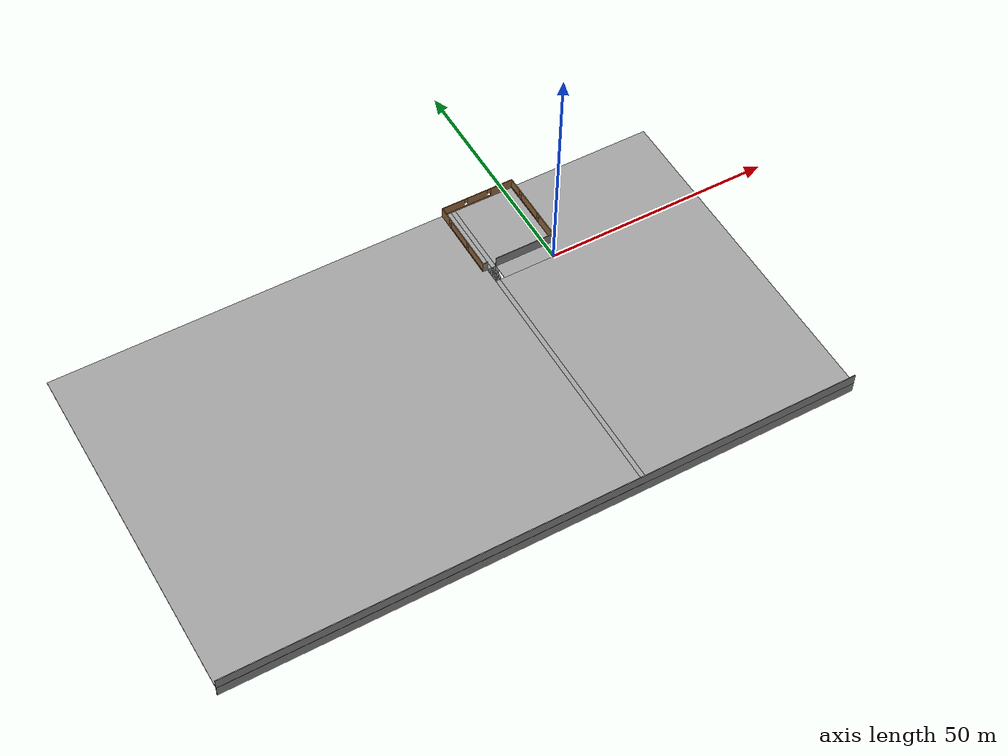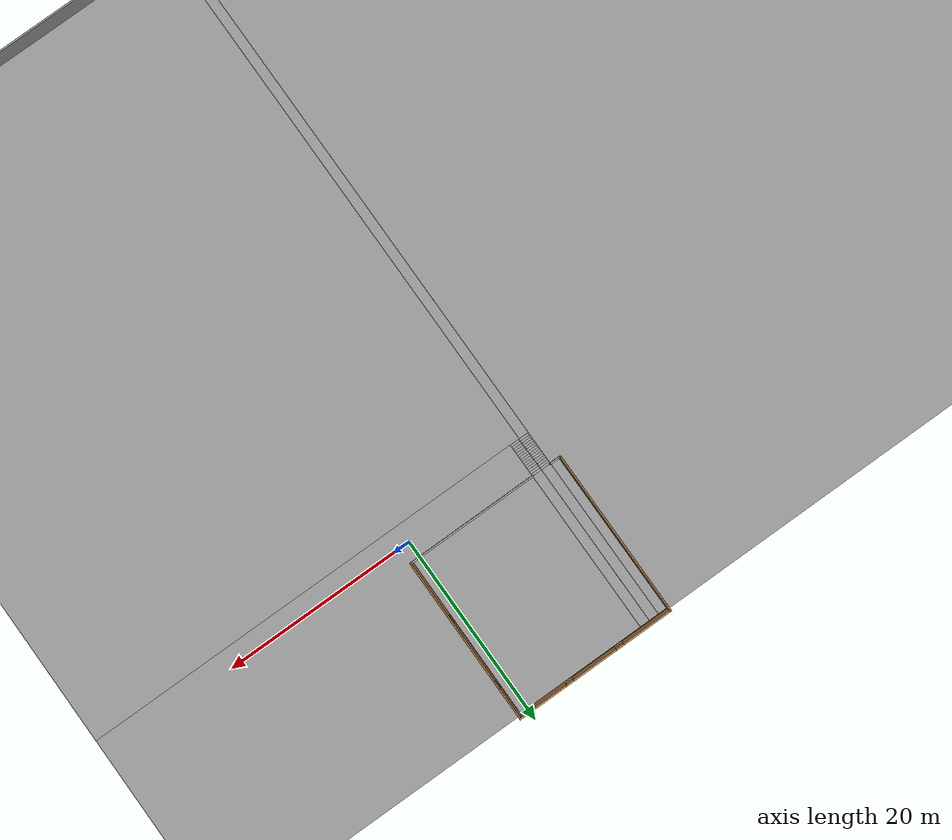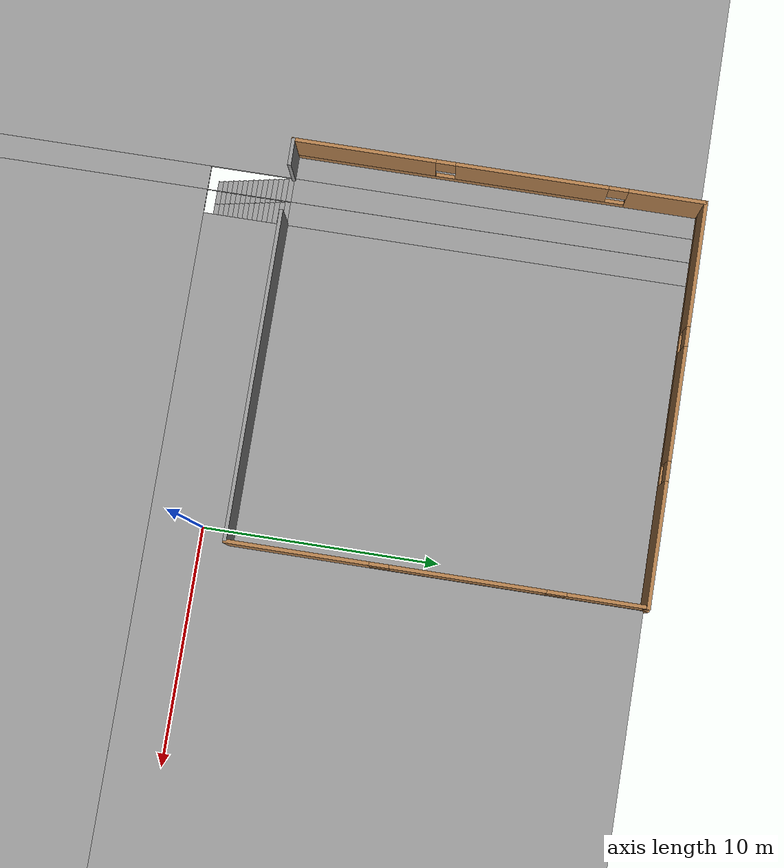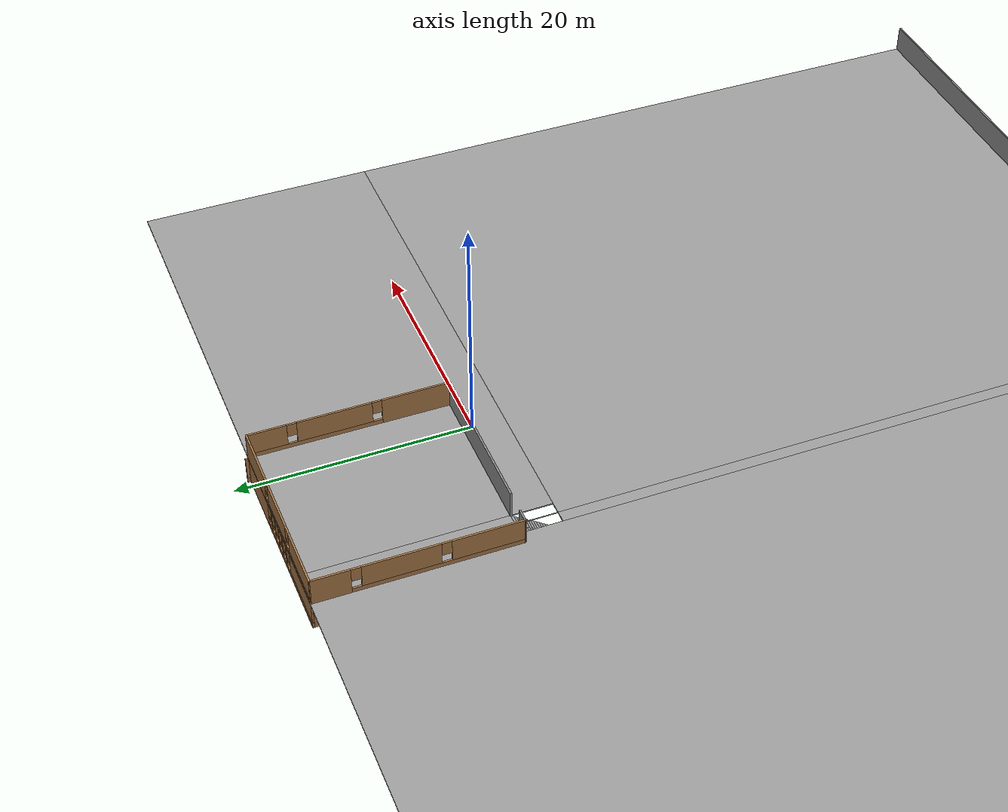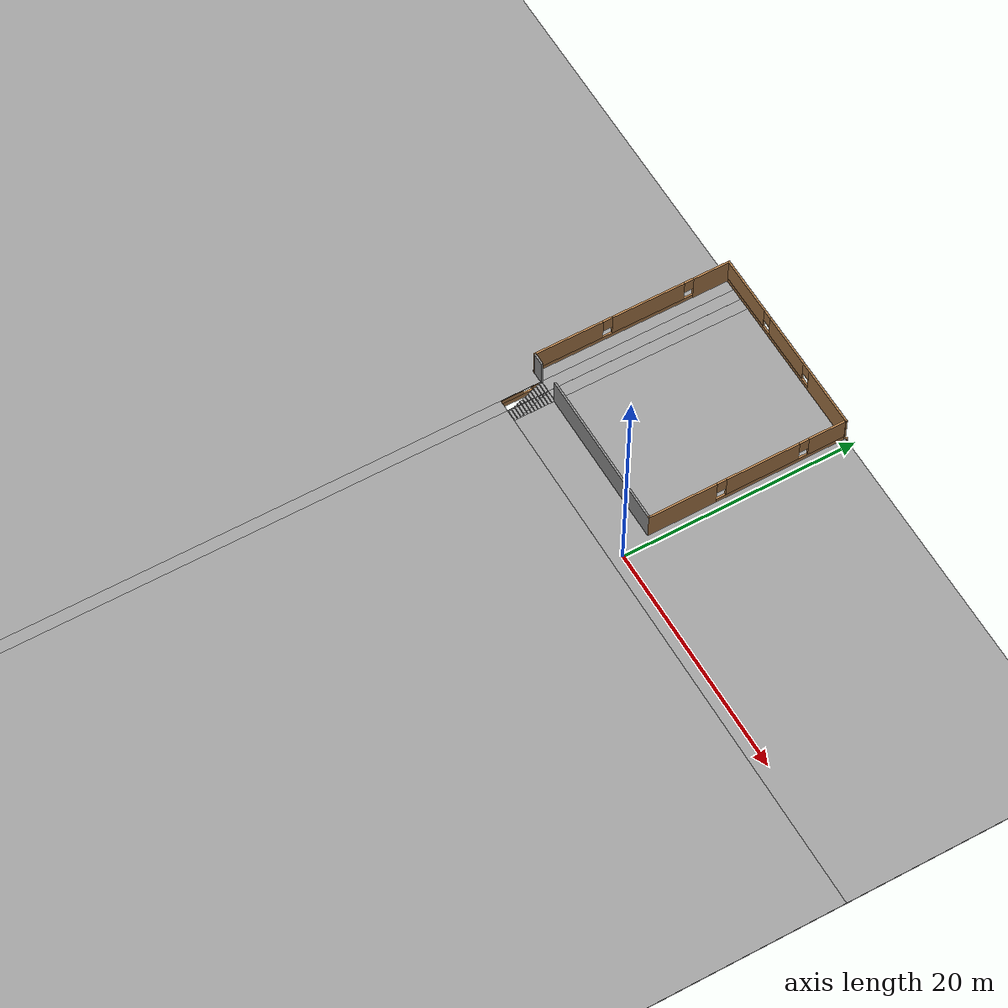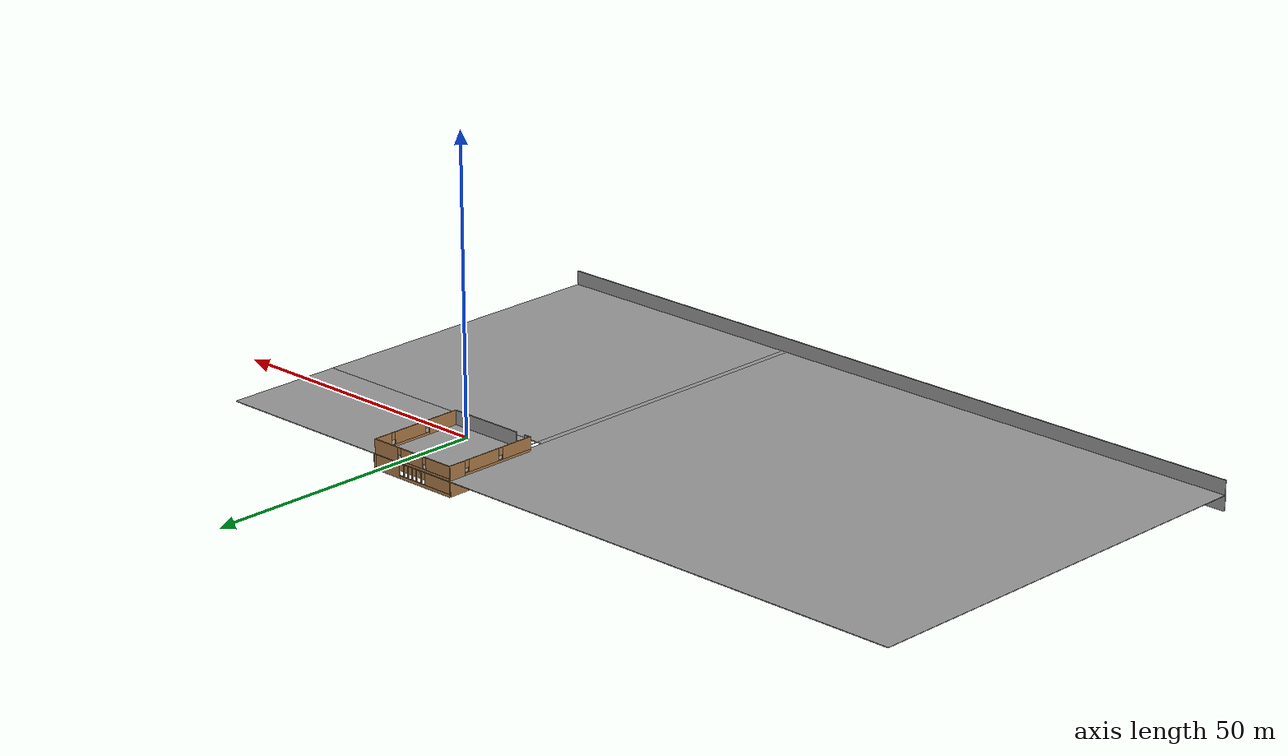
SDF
<?xml version='1.0'?>
<sdf version='1.7'>
  <model name='Floor_Plan_RS1'>
    <pose>-35.0156 -19.3457 0 0 -0 0</pose>
    <link name='Floor_1'>
      <pose>0 -0.124965 2.5 0 -0 0</pose>
      <visual name='Floor_1_Visual_0'>
        <pose>-23.8629 0 0.05 0 -0 0</pose>
        <geometry>
          <box>
            <size>88.2742 75.889 0.1</size>
          </box>
        </geometry>
        <material>
          <script>
            <uri>file://media/materials/scripts/gazebo.material</uri>
            <name>Gazebo/Grey</name>
          </script>
          <ambient>1 1 1 1</ambient>
        </material>
        <meta>
          <layer>1</layer>
        </meta>
      </visual>
      <collision name='Floor_1_Collision_0'>
        <geometry>
          <box>
            <size>88.2742 75.889 0.1</size>
          </box>
        </geometry>
        <pose>-23.8629 0 0.05 0 -0 0</pose>
      </collision>
      <visual name='Floor_1_Visual_1'>
        <pose>20.7753 -10.1559 0.05 0 -0 0</pose>
        <geometry>
          <box>
            <size>1.00207 55.5771 0.1</size>
          </box>
        </geometry>
        <material>
          <script>
            <uri>file://media/materials/scripts/gazebo.material</uri>
            <name>Gazebo/Grey</name>
          </script>
          <ambient>1 1 1 1</ambient>
        </material>
        <meta>
          <layer>1</layer>
        </meta>
      </visual>
      <collision name='Floor_1_Collision_1'>
        <geometry>
          <box>
            <size>1.00207 55.5771 0.1</size>
          </box>
        </geometry>
        <pose>20.7753 -10.1559 0.05 0 -0 0</pose>
      </collision>
      <visual name='Floor_1_Visual_2'>
        <pose>44.6381 -10.1563 0.05 0 -0 0</pose>
        <geometry>
          <box>
            <size>46.7237 55.5763 0.1</size>
          </box>
        </geometry>
        <material>
          <script>
            <uri>file://media/materials/scripts/gazebo.material</uri>
            <name>Gazebo/Grey</name>
          </script>
          <ambient>1 1 1 1</ambient>
        </material>
        <meta>
          <layer>1</layer>
        </meta>
      </visual>
      <collision name='Floor_1_Collision_2'>
        <geometry>
          <box>
            <size>46.7237 55.5763 0.1</size>
          </box>
        </geometry>
        <pose>44.6381 -10.1563 0.05 0 -0 0</pose>
      </collision>
      <visual name='Floor_1_Visual_3'>
        <pose>45.1381 27.7882 0.05 0 -0 0</pose>
        <geometry>
          <box>
            <size>45.7237 20.3126 0.1</size>
          </box>
        </geometry>
        <material>
          <script>
            <uri>file://media/materials/scripts/gazebo.material</uri>
            <name>Gazebo/Grey</name>
          </script>
          <ambient>1 1 1 1</ambient>
        </material>
        <meta>
          <layer>1</layer>
        </meta>
      </visual>
      <collision name='Floor_1_Collision_3'>
        <geometry>
          <box>
            <size>45.7237 20.3126 0.1</size>
          </box>
        </geometry>
        <pose>45.1381 27.7882 0.05 0 -0 0</pose>
      </collision>
      <visual name='Floor_1_Visual_4'>
        <pose>21.2753 27.7886 0.05 0 -0 0</pose>
        <geometry>
          <box>
            <size>0.002066 20.3118 0.1</size>
          </box>
        </geometry>
        <material>
          <script>
            <uri>file://media/materials/scripts/gazebo.material</uri>
            <name>Gazebo/Grey</name>
          </script>
          <ambient>1 1 1 1</ambient>
        </material>
        <meta>
          <layer>1</layer>
        </meta>
      </visual>
      <collision name='Floor_1_Collision_4'>
        <geometry>
          <box>
            <size>0.002066 20.3118 0.1</size>
          </box>
        </geometry>
        <pose>21.2753 27.7886 0.05 0 -0 0</pose>
      </collision>
      <visual name='Floor_1_Visual_5'>
        <pose>21.2753 27.7886 0.05 0 -0 0</pose>
        <geometry>
          <box>
            <size>0.002066 20.3118 0.1</size>
          </box>
        </geometry>
        <material>
          <script>
            <uri>file://media/materials/scripts/gazebo.material</uri>
            <name>Gazebo/Grey</name>
          </script>
          <ambient>1 1 1 1</ambient>
        </material>
        <meta>
          <layer>1</layer>
        </meta>
      </visual>
      <collision name='Floor_1_Collision_5'>
        <geometry>
          <box>
            <size>0.002066 20.3118 0.1</size>
          </box>
        </geometry>
        <pose>21.2753 27.7886 0.05 0 -0 0</pose>
      </collision>
      <visual name='Floor_1_Visual_6'>
        <pose>21.7763 29.5382 0.05 0 -0 0</pose>
        <geometry>
          <box>
            <size>1 16.8126 0.1</size>
          </box>
        </geometry>
        <material>
          <script>
            <uri>file://media/materials/scripts/gazebo.material</uri>
            <name>Gazebo/Grey</name>
          </script>
          <ambient>1 1 1 1</ambient>
        </material>
        <meta>
          <layer>1</layer>
        </meta>
      </visual>
      <collision name='Floor_1_Collision_6'>
        <geometry>
          <box>
            <size>1 16.8126 0.1</size>
          </box>
        </geometry>
        <pose>21.7763 29.5382 0.05 0 -0 0</pose>
      </collision>
      <visual name='Floor_1_Visual_7'>
        <pose>21.7763 29.5382 0.05 0 -0 0</pose>
        <geometry>
          <box>
            <size>1 16.8126 0.1</size>
          </box>
        </geometry>
        <material>
          <script>
            <uri>file://media/materials/scripts/gazebo.material</uri>
            <name>Gazebo/Grey</name>
          </script>
          <ambient>1 1 1 1</ambient>
        </material>
        <meta>
          <layer>1</layer>
        </meta>
      </visual>
      <collision name='Floor_1_Collision_7'>
        <geometry>
          <box>
            <size>1 16.8126 0.1</size>
          </box>
        </geometry>
        <pose>21.7763 29.5382 0.05 0 -0 0</pose>
      </collision>
      <visual name='Floor_1_Visual_8'>
        <pose>20.7742 29.5386 0.05 0 -0 0</pose>
        <geometry>
          <box>
            <size>1 16.8118 0.1</size>
          </box>
        </geometry>
        <material>
          <script>
            <uri>file://media/materials/scripts/gazebo.material</uri>
            <name>Gazebo/Grey</name>
          </script>
          <ambient>1 1 1 1</ambient>
        </material>
        <meta>
          <layer>1</layer>
        </meta>
      </visual>
      <collision name='Floor_1_Collision_8'>
        <geometry>
          <box>
            <size>1 16.8118 0.1</size>
          </box>
        </geometry>
        <pose>20.7742 29.5386 0.05 0 -0 0</pose>
      </collision>
    </link>
    <link name='Stairs_0'>
      <visual name='Stairs_0_Visual_0'>
        <pose>20.7742 17.6244 0.083333 0 -0 -3.14159</pose>
        <geometry>
          <box>
            <size>1 0.233333 0.166667</size>
          </box>
        </geometry>
        <material>
          <script>
            <uri>file://media/materials/scripts/gazebo.material</uri>
            <name>Gazebo/Grey</name>
          </script>
          <ambient>1 1 1 1</ambient>
        </material>
        <meta>
          <layer>0</layer>
        </meta>
      </visual>
      <collision name='Stairs_0_Collision_0'>
        <geometry>
          <box>
            <size>1 0.233333 0.166667</size>
          </box>
        </geometry>
        <pose>20.7742 17.6244 0.083333 0 -0 -3.14159</pose>
      </collision>
      <visual name='Stairs_0_Visual_1'>
        <pose>20.7742 17.8577 0.25 0 -0 -3.14159</pose>
        <geometry>
          <box>
            <size>1 0.233333 0.166667</size>
          </box>
        </geometry>
        <material>
          <script>
            <uri>file://media/materials/scripts/gazebo.material</uri>
            <name>Gazebo/Grey</name>
          </script>
          <ambient>1 1 1 1</ambient>
        </material>
        <meta>
          <layer>0</layer>
        </meta>
      </visual>
      <collision name='Stairs_0_Collision_1'>
        <geometry>
          <box>
            <size>1 0.233333 0.166667</size>
          </box>
        </geometry>
        <pose>20.7742 17.8577 0.25 0 -0 -3.14159</pose>
      </collision>
      <visual name='Stairs_0_Visual_2'>
        <pose>20.7742 18.091 0.416667 0 -0 -3.14159</pose>
        <geometry>
          <box>
            <size>1 0.233333 0.166667</size>
          </box>
        </geometry>
        <material>
          <script>
            <uri>file://media/materials/scripts/gazebo.material</uri>
            <name>Gazebo/Grey</name>
          </script>
          <ambient>1 1 1 1</ambient>
        </material>
        <meta>
          <layer>0</layer>
        </meta>
      </visual>
      <collision name='Stairs_0_Collision_2'>
        <geometry>
          <box>
            <size>1 0.233333 0.166667</size>
          </box>
        </geometry>
        <pose>20.7742 18.091 0.416667 0 -0 -3.14159</pose>
      </collision>
      <visual name='Stairs_0_Visual_3'>
        <pose>20.7742 18.3244 0.583333 0 -0 -3.14159</pose>
        <geometry>
          <box>
            <size>1 0.233333 0.166667</size>
          </box>
        </geometry>
        <material>
          <script>
            <uri>file://media/materials/scripts/gazebo.material</uri>
            <name>Gazebo/Grey</name>
          </script>
          <ambient>1 1 1 1</ambient>
        </material>
        <meta>
          <layer>0</layer>
        </meta>
      </visual>
      <collision name='Stairs_0_Collision_3'>
        <geometry>
          <box>
            <size>1 0.233333 0.166667</size>
          </box>
        </geometry>
        <pose>20.7742 18.3244 0.583333 0 -0 -3.14159</pose>
      </collision>
      <visual name='Stairs_0_Visual_4'>
        <pose>20.7742 18.5577 0.75 0 -0 -3.14159</pose>
        <geometry>
          <box>
            <size>1 0.233333 0.166667</size>
          </box>
        </geometry>
        <material>
          <script>
            <uri>file://media/materials/scripts/gazebo.material</uri>
            <name>Gazebo/Grey</name>
          </script>
          <ambient>1 1 1 1</ambient>
        </material>
        <meta>
          <layer>0</layer>
        </meta>
      </visual>
      <collision name='Stairs_0_Collision_4'>
        <geometry>
          <box>
            <size>1 0.233333 0.166667</size>
          </box>
        </geometry>
        <pose>20.7742 18.5577 0.75 0 -0 -3.14159</pose>
      </collision>
      <visual name='Stairs_0_Visual_5'>
        <pose>20.7742 18.791 0.916667 0 -0 -3.14159</pose>
        <geometry>
          <box>
            <size>1 0.233333 0.166667</size>
          </box>
        </geometry>
        <material>
          <script>
            <uri>file://media/materials/scripts/gazebo.material</uri>
            <name>Gazebo/Grey</name>
          </script>
          <ambient>1 1 1 1</ambient>
        </material>
        <meta>
          <layer>0</layer>
        </meta>
      </visual>
      <collision name='Stairs_0_Collision_5'>
        <geometry>
          <box>
            <size>1 0.233333 0.166667</size>
          </box>
        </geometry>
        <pose>20.7742 18.791 0.916667 0 -0 -3.14159</pose>
      </collision>
      <visual name='Stairs_0_Visual_6'>
        <pose>20.7742 19.0244 1.08333 0 -0 -3.14159</pose>
        <geometry>
          <box>
            <size>1 0.233333 0.166667</size>
          </box>
        </geometry>
        <material>
          <script>
            <uri>file://media/materials/scripts/gazebo.material</uri>
            <name>Gazebo/Grey</name>
          </script>
          <ambient>1 1 1 1</ambient>
        </material>
        <meta>
          <layer>0</layer>
        </meta>
      </visual>
      <collision name='Stairs_0_Collision_6'>
        <geometry>
          <box>
            <size>1 0.233333 0.166667</size>
          </box>
        </geometry>
        <pose>20.7742 19.0244 1.08333 0 -0 -3.14159</pose>
      </collision>
      <visual name='Stairs_0_Visual_7'>
        <pose>20.7742 19.2577 1.25 0 -0 -3.14159</pose>
        <geometry>
          <box>
            <size>1 0.233333 0.166667</size>
          </box>
        </geometry>
        <material>
          <script>
            <uri>file://media/materials/scripts/gazebo.material</uri>
            <name>Gazebo/Grey</name>
          </script>
          <ambient>1 1 1 1</ambient>
        </material>
        <meta>
          <layer>0</layer>
        </meta>
      </visual>
      <collision name='Stairs_0_Collision_7'>
        <geometry>
          <box>
            <size>1 0.233333 0.166667</size>
          </box>
        </geometry>
        <pose>20.7742 19.2577 1.25 0 -0 -3.14159</pose>
      </collision>
      <visual name='Stairs_0_Visual_8'>
        <pose>20.7742 19.491 1.41667 0 -0 -3.14159</pose>
        <geometry>
          <box>
            <size>1 0.233333 0.166667</size>
          </box>
        </geometry>
        <material>
          <script>
            <uri>file://media/materials/scripts/gazebo.material</uri>
            <name>Gazebo/Grey</name>
          </script>
          <ambient>1 1 1 1</ambient>
        </material>
        <meta>
          <layer>0</layer>
        </meta>
      </visual>
      <collision name='Stairs_0_Collision_8'>
        <geometry>
          <box>
            <size>1 0.233333 0.166667</size>
          </box>
        </geometry>
        <pose>20.7742 19.491 1.41667 0 -0 -3.14159</pose>
      </collision>
      <visual name='Stairs_0_Visual_9'>
        <pose>20.7742 19.7244 1.58333 0 -0 -3.14159</pose>
        <geometry>
          <box>
            <size>1 0.233333 0.166667</size>
          </box>
        </geometry>
        <material>
          <script>
            <uri>file://media/materials/scripts/gazebo.material</uri>
            <name>Gazebo/Grey</name>
          </script>
          <ambient>1 1 1 1</ambient>
        </material>
        <meta>
          <layer>0</layer>
        </meta>
      </visual>
      <collision name='Stairs_0_Collision_9'>
        <geometry>
          <box>
            <size>1 0.233333 0.166667</size>
          </box>
        </geometry>
        <pose>20.7742 19.7244 1.58333 0 -0 -3.14159</pose>
      </collision>
      <visual name='Stairs_0_Visual_10'>
        <pose>20.7742 19.9577 1.75 0 -0 -3.14159</pose>
        <geometry>
          <box>
            <size>1 0.233333 0.166667</size>
          </box>
        </geometry>
        <material>
          <script>
            <uri>file://media/materials/scripts/gazebo.material</uri>
            <name>Gazebo/Grey</name>
          </script>
          <ambient>1 1 1 1</ambient>
        </material>
        <meta>
          <layer>0</layer>
        </meta>
      </visual>
      <collision name='Stairs_0_Collision_10'>
        <geometry>
          <box>
            <size>1 0.233333 0.166667</size>
          </box>
        </geometry>
        <pose>20.7742 19.9577 1.75 0 -0 -3.14159</pose>
      </collision>
      <visual name='Stairs_0_Visual_11'>
        <pose>20.7742 20.191 1.91667 0 -0 -3.14159</pose>
        <geometry>
          <box>
            <size>1 0.233333 0.166667</size>
          </box>
        </geometry>
        <material>
          <script>
            <uri>file://media/materials/scripts/gazebo.material</uri>
            <name>Gazebo/Grey</name>
          </script>
          <ambient>1 1 1 1</ambient>
        </material>
        <meta>
          <layer>0</layer>
        </meta>
      </visual>
      <collision name='Stairs_0_Collision_11'>
        <geometry>
          <box>
            <size>1 0.233333 0.166667</size>
          </box>
        </geometry>
        <pose>20.7742 20.191 1.91667 0 -0 -3.14159</pose>
      </collision>
      <visual name='Stairs_0_Visual_12'>
        <pose>20.7742 20.4244 2.08333 0 -0 -3.14159</pose>
        <geometry>
          <box>
            <size>1 0.233333 0.166667</size>
          </box>
        </geometry>
        <material>
          <script>
            <uri>file://media/materials/scripts/gazebo.material</uri>
            <name>Gazebo/Grey</name>
          </script>
          <ambient>1 1 1 1</ambient>
        </material>
        <meta>
          <layer>0</layer>
        </meta>
      </visual>
      <collision name='Stairs_0_Collision_12'>
        <geometry>
          <box>
            <size>1 0.233333 0.166667</size>
          </box>
        </geometry>
        <pose>20.7742 20.4244 2.08333 0 -0 -3.14159</pose>
      </collision>
      <visual name='Stairs_0_Visual_13'>
        <pose>20.7742 20.6577 2.25 0 -0 -3.14159</pose>
        <geometry>
          <box>
            <size>1 0.233333 0.166667</size>
          </box>
        </geometry>
        <material>
          <script>
            <uri>file://media/materials/scripts/gazebo.material</uri>
            <name>Gazebo/Grey</name>
          </script>
          <ambient>1 1 1 1</ambient>
        </material>
        <meta>
          <layer>0</layer>
        </meta>
      </visual>
      <collision name='Stairs_0_Collision_13'>
        <geometry>
          <box>
            <size>1 0.233333 0.166667</size>
          </box>
        </geometry>
        <pose>20.7742 20.6577 2.25 0 -0 -3.14159</pose>
      </collision>
      <visual name='Stairs_0_Visual_14'>
        <pose>20.7742 20.891 2.41667 0 -0 -3.14159</pose>
        <geometry>
          <box>
            <size>1 0.233333 0.166667</size>
          </box>
        </geometry>
        <material>
          <script>
            <uri>file://media/materials/scripts/gazebo.material</uri>
            <name>Gazebo/Grey</name>
          </script>
          <ambient>1 1 1 1</ambient>
        </material>
        <meta>
          <layer>0</layer>
        </meta>
      </visual>
      <collision name='Stairs_0_Collision_14'>
        <geometry>
          <box>
            <size>1 0.233333 0.166667</size>
          </box>
        </geometry>
        <pose>20.7742 20.891 2.41667 0 -0 -3.14159</pose>
      </collision>
    </link>
    <link name='Stairs_2'>
      <visual name='Stairs_2_Visual_0'>
        <pose>21.7763 17.6235 0.083333 0 -0 -3.14159</pose>
        <geometry>
          <box>
            <size>1 0.233333 0.166667</size>
          </box>
        </geometry>
        <material>
          <script>
            <uri>file://media/materials/scripts/gazebo.material</uri>
            <name>Gazebo/Grey</name>
          </script>
          <ambient>1 1 1 1</ambient>
        </material>
        <meta>
          <layer>0</layer>
        </meta>
      </visual>
      <collision name='Stairs_2_Collision_0'>
        <geometry>
          <box>
            <size>1 0.233333 0.166667</size>
          </box>
        </geometry>
        <pose>21.7763 17.6235 0.083333 0 -0 -3.14159</pose>
      </collision>
      <visual name='Stairs_2_Visual_1'>
        <pose>21.7763 17.8569 0.25 0 -0 -3.14159</pose>
        <geometry>
          <box>
            <size>1 0.233333 0.166667</size>
          </box>
        </geometry>
        <material>
          <script>
            <uri>file://media/materials/scripts/gazebo.material</uri>
            <name>Gazebo/Grey</name>
          </script>
          <ambient>1 1 1 1</ambient>
        </material>
        <meta>
          <layer>0</layer>
        </meta>
      </visual>
      <collision name='Stairs_2_Collision_1'>
        <geometry>
          <box>
            <size>1 0.233333 0.166667</size>
          </box>
        </geometry>
        <pose>21.7763 17.8569 0.25 0 -0 -3.14159</pose>
      </collision>
      <visual name='Stairs_2_Visual_2'>
        <pose>21.7763 18.0902 0.416667 0 -0 -3.14159</pose>
        <geometry>
          <box>
            <size>1 0.233333 0.166667</size>
          </box>
        </geometry>
        <material>
          <script>
            <uri>file://media/materials/scripts/gazebo.material</uri>
            <name>Gazebo/Grey</name>
          </script>
          <ambient>1 1 1 1</ambient>
        </material>
        <meta>
          <layer>0</layer>
        </meta>
      </visual>
      <collision name='Stairs_2_Collision_2'>
        <geometry>
          <box>
            <size>1 0.233333 0.166667</size>
          </box>
        </geometry>
        <pose>21.7763 18.0902 0.416667 0 -0 -3.14159</pose>
      </collision>
      <visual name='Stairs_2_Visual_3'>
        <pose>21.7763 18.3235 0.583333 0 -0 -3.14159</pose>
        <geometry>
          <box>
            <size>1 0.233333 0.166667</size>
          </box>
        </geometry>
        <material>
          <script>
            <uri>file://media/materials/scripts/gazebo.material</uri>
            <name>Gazebo/Grey</name>
          </script>
          <ambient>1 1 1 1</ambient>
        </material>
        <meta>
          <layer>0</layer>
        </meta>
      </visual>
      <collision name='Stairs_2_Collision_3'>
        <geometry>
          <box>
            <size>1 0.233333 0.166667</size>
          </box>
        </geometry>
        <pose>21.7763 18.3235 0.583333 0 -0 -3.14159</pose>
      </collision>
      <visual name='Stairs_2_Visual_4'>
        <pose>21.7763 18.5569 0.75 0 -0 -3.14159</pose>
        <geometry>
          <box>
            <size>1 0.233333 0.166667</size>
          </box>
        </geometry>
        <material>
          <script>
            <uri>file://media/materials/scripts/gazebo.material</uri>
            <name>Gazebo/Grey</name>
          </script>
          <ambient>1 1 1 1</ambient>
        </material>
        <meta>
          <layer>0</layer>
        </meta>
      </visual>
      <collision name='Stairs_2_Collision_4'>
        <geometry>
          <box>
            <size>1 0.233333 0.166667</size>
          </box>
        </geometry>
        <pose>21.7763 18.5569 0.75 0 -0 -3.14159</pose>
      </collision>
      <visual name='Stairs_2_Visual_5'>
        <pose>21.7763 18.7902 0.916667 0 -0 -3.14159</pose>
        <geometry>
          <box>
            <size>1 0.233333 0.166667</size>
          </box>
        </geometry>
        <material>
          <script>
            <uri>file://media/materials/scripts/gazebo.material</uri>
            <name>Gazebo/Grey</name>
          </script>
          <ambient>1 1 1 1</ambient>
        </material>
        <meta>
          <layer>0</layer>
        </meta>
      </visual>
      <collision name='Stairs_2_Collision_5'>
        <geometry>
          <box>
            <size>1 0.233333 0.166667</size>
          </box>
        </geometry>
        <pose>21.7763 18.7902 0.916667 0 -0 -3.14159</pose>
      </collision>
      <visual name='Stairs_2_Visual_6'>
        <pose>21.7763 19.0235 1.08333 0 -0 -3.14159</pose>
        <geometry>
          <box>
            <size>1 0.233333 0.166667</size>
          </box>
        </geometry>
        <material>
          <script>
            <uri>file://media/materials/scripts/gazebo.material</uri>
            <name>Gazebo/Grey</name>
          </script>
          <ambient>1 1 1 1</ambient>
        </material>
        <meta>
          <layer>0</layer>
        </meta>
      </visual>
      <collision name='Stairs_2_Collision_6'>
        <geometry>
          <box>
            <size>1 0.233333 0.166667</size>
          </box>
        </geometry>
        <pose>21.7763 19.0235 1.08333 0 -0 -3.14159</pose>
      </collision>
      <visual name='Stairs_2_Visual_7'>
        <pose>21.7763 19.2569 1.25 0 -0 -3.14159</pose>
        <geometry>
          <box>
            <size>1 0.233333 0.166667</size>
          </box>
        </geometry>
        <material>
          <script>
            <uri>file://media/materials/scripts/gazebo.material</uri>
            <name>Gazebo/Grey</name>
          </script>
          <ambient>1 1 1 1</ambient>
        </material>
        <meta>
          <layer>0</layer>
        </meta>
      </visual>
      <collision name='Stairs_2_Collision_7'>
        <geometry>
          <box>
            <size>1 0.233333 0.166667</size>
          </box>
        </geometry>
        <pose>21.7763 19.2569 1.25 0 -0 -3.14159</pose>
      </collision>
      <visual name='Stairs_2_Visual_8'>
        <pose>21.7763 19.4902 1.41667 0 -0 -3.14159</pose>
        <geometry>
          <box>
            <size>1 0.233333 0.166667</size>
          </box>
        </geometry>
        <material>
          <script>
            <uri>file://media/materials/scripts/gazebo.material</uri>
            <name>Gazebo/Grey</name>
          </script>
          <ambient>1 1 1 1</ambient>
        </material>
        <meta>
          <layer>0</layer>
        </meta>
      </visual>
      <collision name='Stairs_2_Collision_8'>
        <geometry>
          <box>
            <size>1 0.233333 0.166667</size>
          </box>
        </geometry>
        <pose>21.7763 19.4902 1.41667 0 -0 -3.14159</pose>
      </collision>
      <visual name='Stairs_2_Visual_9'>
        <pose>21.7763 19.7235 1.58333 0 -0 -3.14159</pose>
        <geometry>
          <box>
            <size>1 0.233333 0.166667</size>
          </box>
        </geometry>
        <material>
          <script>
            <uri>file://media/materials/scripts/gazebo.material</uri>
            <name>Gazebo/Grey</name>
          </script>
          <ambient>1 1 1 1</ambient>
        </material>
        <meta>
          <layer>0</layer>
        </meta>
      </visual>
      <collision name='Stairs_2_Collision_9'>
        <geometry>
          <box>
            <size>1 0.233333 0.166667</size>
          </box>
        </geometry>
        <pose>21.7763 19.7235 1.58333 0 -0 -3.14159</pose>
      </collision>
      <visual name='Stairs_2_Visual_10'>
        <pose>21.7763 19.9569 1.75 0 -0 -3.14159</pose>
        <geometry>
          <box>
            <size>1 0.233333 0.166667</size>
          </box>
        </geometry>
        <material>
          <script>
            <uri>file://media/materials/scripts/gazebo.material</uri>
            <name>Gazebo/Grey</name>
          </script>
          <ambient>1 1 1 1</ambient>
        </material>
        <meta>
          <layer>0</layer>
        </meta>
      </visual>
      <collision name='Stairs_2_Collision_10'>
        <geometry>
          <box>
            <size>1 0.233333 0.166667</size>
          </box>
        </geometry>
        <pose>21.7763 19.9569 1.75 0 -0 -3.14159</pose>
      </collision>
      <visual name='Stairs_2_Visual_11'>
        <pose>21.7763 20.1902 1.91667 0 -0 -3.14159</pose>
        <geometry>
          <box>
            <size>1 0.233333 0.166667</size>
          </box>
        </geometry>
        <material>
          <script>
            <uri>file://media/materials/scripts/gazebo.material</uri>
            <name>Gazebo/Grey</name>
          </script>
          <ambient>1 1 1 1</ambient>
        </material>
        <meta>
          <layer>0</layer>
        </meta>
      </visual>
      <collision name='Stairs_2_Collision_11'>
        <geometry>
          <box>
            <size>1 0.233333 0.166667</size>
          </box>
        </geometry>
        <pose>21.7763 20.1902 1.91667 0 -0 -3.14159</pose>
      </collision>
      <visual name='Stairs_2_Visual_12'>
        <pose>21.7763 20.4235 2.08333 0 -0 -3.14159</pose>
        <geometry>
          <box>
            <size>1 0.233333 0.166667</size>
          </box>
        </geometry>
        <material>
          <script>
            <uri>file://media/materials/scripts/gazebo.material</uri>
            <name>Gazebo/Grey</name>
          </script>
          <ambient>1 1 1 1</ambient>
        </material>
        <meta>
          <layer>0</layer>
        </meta>
      </visual>
      <collision name='Stairs_2_Collision_12'>
        <geometry>
          <box>
            <size>1 0.233333 0.166667</size>
          </box>
        </geometry>
        <pose>21.7763 20.4235 2.08333 0 -0 -3.14159</pose>
      </collision>
      <visual name='Stairs_2_Visual_13'>
        <pose>21.7763 20.6569 2.25 0 -0 -3.14159</pose>
        <geometry>
          <box>
            <size>1 0.233333 0.166667</size>
          </box>
        </geometry>
        <material>
          <script>
            <uri>file://media/materials/scripts/gazebo.material</uri>
            <name>Gazebo/Grey</name>
          </script>
          <ambient>1 1 1 1</ambient>
        </material>
        <meta>
          <layer>0</layer>
        </meta>
      </visual>
      <collision name='Stairs_2_Collision_13'>
        <geometry>
          <box>
            <size>1 0.233333 0.166667</size>
          </box>
        </geometry>
        <pose>21.7763 20.6569 2.25 0 -0 -3.14159</pose>
      </collision>
      <visual name='Stairs_2_Visual_14'>
        <pose>21.7763 20.8902 2.41667 0 -0 -3.14159</pose>
        <geometry>
          <box>
            <size>1 0.233333 0.166667</size>
          </box>
        </geometry>
        <material>
          <script>
            <uri>file://media/materials/scripts/gazebo.material</uri>
            <name>Gazebo/Grey</name>
          </script>
          <ambient>1 1 1 1</ambient>
        </material>
        <meta>
          <layer>0</layer>
        </meta>
      </visual>
      <collision name='Stairs_2_Collision_14'>
        <geometry>
          <box>
            <size>1 0.233333 0.166667</size>
          </box>
        </geometry>
        <pose>21.7763 20.8902 2.41667 0 -0 -3.14159</pose>
      </collision>
    </link>
    <link name='Wall_10'>
      <pose>27.477 37.7444 0 0 -0 3.14159</pose>
      <visual name='Wall_10_Visual_0'>
        <pose>-5.5452 0 1.25 0 -0 0</pose>
        <geometry>
          <box>
            <size>5.40959 0.15 2.5</size>
          </box>
        </geometry>
        <material>
          <script>
            <uri>file://media/materials/scripts/gazebo.material</uri>
            <name>Gazebo/Wood</name>
          </script>
          <ambient>1 1 1 1</ambient>
        </material>
        <meta>
          <layer>0</layer>
        </meta>
      </visual>
      <collision name='Wall_10_Collision_0'>
        <geometry>
          <box>
            <size>5.40959 0.15 2.5</size>
          </box>
        </geometry>
        <pose>-5.5452 0 1.25 0 -0 0</pose>
      </collision>
      <visual name='Wall_10_Visual_1'>
        <pose>2.7048 0 0.25 0 -0 0</pose>
        <geometry>
          <box>
            <size>11.0904 0.15 0.5</size>
          </box>
        </geometry>
        <material>
          <script>
            <uri>file://media/materials/scripts/gazebo.material</uri>
            <name>Gazebo/Wood</name>
          </script>
          <ambient>1 1 1 1</ambient>
        </material>
        <meta>
          <layer>0</layer>
        </meta>
      </visual>
      <collision name='Wall_10_Collision_1'>
        <geometry>
          <box>
            <size>11.0904 0.15 0.5</size>
          </box>
        </geometry>
        <pose>2.7048 0 0.25 0 -0 0</pose>
      </collision>
      <visual name='Wall_10_Visual_2'>
        <pose>-1.94818 0 1.5 0 -0 0</pose>
        <geometry>
          <box>
            <size>0.184446 0.15 2</size>
          </box>
        </geometry>
        <material>
          <script>
            <uri>file://media/materials/scripts/gazebo.material</uri>
            <name>Gazebo/Wood</name>
          </script>
          <ambient>1 1 1 1</ambient>
        </material>
        <meta>
          <layer>0</layer>
        </meta>
      </visual>
      <collision name='Wall_10_Collision_2'>
        <geometry>
          <box>
            <size>0.184446 0.15 2</size>
          </box>
        </geometry>
        <pose>-1.94818 0 1.5 0 -0 0</pose>
      </collision>
      <visual name='Wall_10_Visual_3'>
        <pose>-0.994502 0 1.5 0 -0 0</pose>
        <geometry>
          <box>
            <size>0.122918 0.15 2</size>
          </box>
        </geometry>
        <material>
          <script>
            <uri>file://media/materials/scripts/gazebo.material</uri>
            <name>Gazebo/Wood</name>
          </script>
          <ambient>1 1 1 1</ambient>
        </material>
        <meta>
          <layer>0</layer>
        </meta>
      </visual>
      <collision name='Wall_10_Collision_3'>
        <geometry>
          <box>
            <size>0.122918 0.15 2</size>
          </box>
        </geometry>
        <pose>-0.994502 0 1.5 0 -0 0</pose>
      </collision>
      <visual name='Wall_10_Visual_4'>
        <pose>-0.071584 0 1.5 0 -0 0</pose>
        <geometry>
          <box>
            <size>0.122918 0.15 2</size>
          </box>
        </geometry>
        <material>
          <script>
            <uri>file://media/materials/scripts/gazebo.material</uri>
            <name>Gazebo/Wood</name>
          </script>
          <ambient>1 1 1 1</ambient>
        </material>
        <meta>
          <layer>0</layer>
        </meta>
      </visual>
      <collision name='Wall_10_Collision_4'>
        <geometry>
          <box>
            <size>0.122918 0.15 2</size>
          </box>
        </geometry>
        <pose>-0.071584 0 1.5 0 -0 0</pose>
      </collision>
      <visual name='Wall_10_Visual_5'>
        <pose>0.882098 0 1.5 0 -0 0</pose>
        <geometry>
          <box>
            <size>0.184447 0.15 2</size>
          </box>
        </geometry>
        <material>
          <script>
            <uri>file://media/materials/scripts/gazebo.material</uri>
            <name>Gazebo/Wood</name>
          </script>
          <ambient>1 1 1 1</ambient>
        </material>
        <meta>
          <layer>0</layer>
        </meta>
      </visual>
      <collision name='Wall_10_Collision_5'>
        <geometry>
          <box>
            <size>0.184447 0.15 2</size>
          </box>
        </geometry>
        <pose>0.882098 0 1.5 0 -0 0</pose>
      </collision>
      <visual name='Wall_10_Visual_6'>
        <pose>1.88137 0 1.5 0 -0 0</pose>
        <geometry>
          <box>
            <size>0.2141 0.15 2</size>
          </box>
        </geometry>
        <material>
          <script>
            <uri>file://media/materials/scripts/gazebo.material</uri>
            <name>Gazebo/Wood</name>
          </script>
          <ambient>1 1 1 1</ambient>
        </material>
        <meta>
          <layer>0</layer>
        </meta>
      </visual>
      <collision name='Wall_10_Collision_6'>
        <geometry>
          <box>
            <size>0.2141 0.15 2</size>
          </box>
        </geometry>
        <pose>1.88137 0 1.5 0 -0 0</pose>
      </collision>
      <visual name='Wall_10_Visual_7'>
        <pose>5.51921 0 1.5 0 -0 0</pose>
        <geometry>
          <box>
            <size>5.46158 0.15 2</size>
          </box>
        </geometry>
        <material>
          <script>
            <uri>file://media/materials/scripts/gazebo.material</uri>
            <name>Gazebo/Wood</name>
          </script>
          <ambient>1 1 1 1</ambient>
        </material>
        <meta>
          <layer>0</layer>
        </meta>
      </visual>
      <collision name='Wall_10_Collision_7'>
        <geometry>
          <box>
            <size>5.46158 0.15 2</size>
          </box>
        </geometry>
        <pose>5.51921 0 1.5 0 -0 0</pose>
      </collision>
      <visual name='Wall_10_Visual_8'>
        <pose>-2.44041 0 1.9 0 -0 0</pose>
        <geometry>
          <box>
            <size>0.8 0.15 1.2</size>
          </box>
        </geometry>
        <material>
          <script>
            <uri>file://media/materials/scripts/gazebo.material</uri>
            <name>Gazebo/Wood</name>
          </script>
          <ambient>1 1 1 1</ambient>
        </material>
        <meta>
          <layer>0</layer>
        </meta>
      </visual>
      <collision name='Wall_10_Collision_8'>
        <geometry>
          <box>
            <size>0.8 0.15 1.2</size>
          </box>
        </geometry>
        <pose>-2.44041 0 1.9 0 -0 0</pose>
      </collision>
      <visual name='Wall_10_Visual_9'>
        <pose>-1.45596 0 1.9 0 -0 0</pose>
        <geometry>
          <box>
            <size>0.8 0.15 1.2</size>
          </box>
        </geometry>
        <material>
          <script>
            <uri>file://media/materials/scripts/gazebo.material</uri>
            <name>Gazebo/Wood</name>
          </script>
          <ambient>1 1 1 1</ambient>
        </material>
        <meta>
          <layer>0</layer>
        </meta>
      </visual>
      <collision name='Wall_10_Collision_9'>
        <geometry>
          <box>
            <size>0.8 0.15 1.2</size>
          </box>
        </geometry>
        <pose>-1.45596 0 1.9 0 -0 0</pose>
      </collision>
      <visual name='Wall_10_Visual_10'>
        <pose>-0.533043 0 1.9 0 -0 0</pose>
        <geometry>
          <box>
            <size>0.8 0.15 1.2</size>
          </box>
        </geometry>
        <material>
          <script>
            <uri>file://media/materials/scripts/gazebo.material</uri>
            <name>Gazebo/Wood</name>
          </script>
          <ambient>1 1 1 1</ambient>
        </material>
        <meta>
          <layer>0</layer>
        </meta>
      </visual>
      <collision name='Wall_10_Collision_10'>
        <geometry>
          <box>
            <size>0.8 0.15 1.2</size>
          </box>
        </geometry>
        <pose>-0.533043 0 1.9 0 -0 0</pose>
      </collision>
      <visual name='Wall_10_Visual_11'>
        <pose>0.389875 0 1.9 0 -0 0</pose>
        <geometry>
          <box>
            <size>0.8 0.15 1.2</size>
          </box>
        </geometry>
        <material>
          <script>
            <uri>file://media/materials/scripts/gazebo.material</uri>
            <name>Gazebo/Wood</name>
          </script>
          <ambient>1 1 1 1</ambient>
        </material>
        <meta>
          <layer>0</layer>
        </meta>
      </visual>
      <collision name='Wall_10_Collision_11'>
        <geometry>
          <box>
            <size>0.8 0.15 1.2</size>
          </box>
        </geometry>
        <pose>0.389875 0 1.9 0 -0 0</pose>
      </collision>
      <visual name='Wall_10_Visual_12'>
        <pose>1.37432 0 1.9 0 -0 0</pose>
        <geometry>
          <box>
            <size>0.8 0.15 1.2</size>
          </box>
        </geometry>
        <material>
          <script>
            <uri>file://media/materials/scripts/gazebo.material</uri>
            <name>Gazebo/Wood</name>
          </script>
          <ambient>1 1 1 1</ambient>
        </material>
        <meta>
          <layer>0</layer>
        </meta>
      </visual>
      <collision name='Wall_10_Collision_12'>
        <geometry>
          <box>
            <size>0.8 0.15 1.2</size>
          </box>
        </geometry>
        <pose>1.37432 0 1.9 0 -0 0</pose>
      </collision>
      <visual name='Wall_10_Visual_13'>
        <pose>2.38842 0 1.9 0 -0 0</pose>
        <geometry>
          <box>
            <size>0.8 0.15 1.2</size>
          </box>
        </geometry>
        <material>
          <script>
            <uri>file://media/materials/scripts/gazebo.material</uri>
            <name>Gazebo/Wood</name>
          </script>
          <ambient>1 1 1 1</ambient>
        </material>
        <meta>
          <layer>0</layer>
        </meta>
      </visual>
      <collision name='Wall_10_Collision_13'>
        <geometry>
          <box>
            <size>0.8 0.15 1.2</size>
          </box>
        </geometry>
        <pose>2.38842 0 1.9 0 -0 0</pose>
      </collision>
    </link>
    <link name='Wall_11'>
      <pose>19.3021 21.1944 0 0 -0 -1.5708</pose>
      <visual name='Wall_11_Visual_0'>
        <pose>-14.7156 0 1.25 0 -0 0</pose>
        <geometry>
          <box>
            <size>3.81882 0.15 2.5</size>
          </box>
        </geometry>
        <material>
          <script>
            <uri>file://media/materials/scripts/gazebo.material</uri>
            <name>Gazebo/Wood</name>
          </script>
          <ambient>1 1 1 1</ambient>
        </material>
        <meta>
          <layer>0</layer>
        </meta>
      </visual>
      <collision name='Wall_11_Collision_0'>
        <geometry>
          <box>
            <size>3.81882 0.15 2.5</size>
          </box>
        </geometry>
        <pose>-14.7156 0 1.25 0 -0 0</pose>
      </collision>
      <visual name='Wall_11_Visual_1'>
        <pose>-7.90963 0 1.25 0 -0 0</pose>
        <geometry>
          <box>
            <size>2.50541 0.15 2.5</size>
          </box>
        </geometry>
        <material>
          <script>
            <uri>file://media/materials/scripts/gazebo.material</uri>
            <name>Gazebo/Wood</name>
          </script>
          <ambient>1 1 1 1</ambient>
        </material>
        <meta>
          <layer>0</layer>
        </meta>
      </visual>
      <collision name='Wall_11_Collision_1'>
        <geometry>
          <box>
            <size>2.50541 0.15 2.5</size>
          </box>
        </geometry>
        <pose>-7.90963 0 1.25 0 -0 0</pose>
      </collision>
      <visual name='Wall_11_Visual_2'>
        <pose>14.3708 0 1.25 0 -0 0</pose>
        <geometry>
          <box>
            <size>4.50842 0.15 2.5</size>
          </box>
        </geometry>
        <material>
          <script>
            <uri>file://media/materials/scripts/gazebo.material</uri>
            <name>Gazebo/Wood</name>
          </script>
          <ambient>1 1 1 1</ambient>
        </material>
        <meta>
          <layer>0</layer>
        </meta>
      </visual>
      <collision name='Wall_11_Collision_2'>
        <geometry>
          <box>
            <size>4.50842 0.15 2.5</size>
          </box>
        </geometry>
        <pose>14.3708 0 1.25 0 -0 0</pose>
      </collision>
      <visual name='Wall_11_Visual_3'>
        <pose>-11.4343 0 0.25 0 -0 0</pose>
        <geometry>
          <box>
            <size>2.74384 0.15 0.5</size>
          </box>
        </geometry>
        <material>
          <script>
            <uri>file://media/materials/scripts/gazebo.material</uri>
            <name>Gazebo/Wood</name>
          </script>
          <ambient>1 1 1 1</ambient>
        </material>
        <meta>
          <layer>0</layer>
        </meta>
      </visual>
      <collision name='Wall_11_Collision_3'>
        <geometry>
          <box>
            <size>2.74384 0.15 0.5</size>
          </box>
        </geometry>
        <pose>-11.4343 0 0.25 0 -0 0</pose>
      </collision>
      <visual name='Wall_11_Visual_4'>
        <pose>2.27982 0 0.25 0 -0 0</pose>
        <geometry>
          <box>
            <size>17.8735 0.15 0.5</size>
          </box>
        </geometry>
        <material>
          <script>
            <uri>file://media/materials/scripts/gazebo.material</uri>
            <name>Gazebo/Wood</name>
          </script>
          <ambient>1 1 1 1</ambient>
        </material>
        <meta>
          <layer>0</layer>
        </meta>
      </visual>
      <collision name='Wall_11_Collision_4'>
        <geometry>
          <box>
            <size>17.8735 0.15 0.5</size>
          </box>
        </geometry>
        <pose>2.27982 0 0.25 0 -0 0</pose>
      </collision>
      <visual name='Wall_11_Visual_5'>
        <pose>-11.0343 0 1.5 0 -0 0</pose>
        <geometry>
          <box>
            <size>1.94384 0.15 2</size>
          </box>
        </geometry>
        <material>
          <script>
            <uri>file://media/materials/scripts/gazebo.material</uri>
            <name>Gazebo/Wood</name>
          </script>
          <ambient>1 1 1 1</ambient>
        </material>
        <meta>
          <layer>0</layer>
        </meta>
      </visual>
      <collision name='Wall_11_Collision_5'>
        <geometry>
          <box>
            <size>1.94384 0.15 2</size>
          </box>
        </geometry>
        <pose>-11.0343 0 1.5 0 -0 0</pose>
      </collision>
      <visual name='Wall_11_Visual_6'>
        <pose>-11.0343 0 1.5 0 -0 0</pose>
        <geometry>
          <box>
            <size>1.94384 0.15 2</size>
          </box>
        </geometry>
        <material>
          <script>
            <uri>file://media/materials/scripts/gazebo.material</uri>
            <name>Gazebo/Wood</name>
          </script>
          <ambient>1 1 1 1</ambient>
        </material>
        <meta>
          <layer>0</layer>
        </meta>
      </visual>
      <collision name='Wall_11_Collision_6'>
        <geometry>
          <box>
            <size>1.94384 0.15 2</size>
          </box>
        </geometry>
        <pose>-11.0343 0 1.5 0 -0 0</pose>
      </collision>
      <visual name='Wall_11_Visual_7'>
        <pose>-2.71707 0 1.5 0 -0 0</pose>
        <geometry>
          <box>
            <size>6.27973 0.15 2</size>
          </box>
        </geometry>
        <material>
          <script>
            <uri>file://media/materials/scripts/gazebo.material</uri>
            <name>Gazebo/Wood</name>
          </script>
          <ambient>1 1 1 1</ambient>
        </material>
        <meta>
          <layer>0</layer>
        </meta>
      </visual>
      <collision name='Wall_11_Collision_7'>
        <geometry>
          <box>
            <size>6.27973 0.15 2</size>
          </box>
        </geometry>
        <pose>-2.71707 0 1.5 0 -0 0</pose>
      </collision>
      <visual name='Wall_11_Visual_8'>
        <pose>3.83674 0 1.5 0 -0 0</pose>
        <geometry>
          <box>
            <size>5.22788 0.15 2</size>
          </box>
        </geometry>
        <material>
          <script>
            <uri>file://media/materials/scripts/gazebo.material</uri>
            <name>Gazebo/Wood</name>
          </script>
          <ambient>1 1 1 1</ambient>
        </material>
        <meta>
          <layer>0</layer>
        </meta>
      </visual>
      <collision name='Wall_11_Collision_8'>
        <geometry>
          <box>
            <size>5.22788 0.15 2</size>
          </box>
        </geometry>
        <pose>3.83674 0 1.5 0 -0 0</pose>
      </collision>
      <visual name='Wall_11_Visual_9'>
        <pose>9.23363 0 1.5 0 -0 0</pose>
        <geometry>
          <box>
            <size>3.9659 0.15 2</size>
          </box>
        </geometry>
        <material>
          <script>
            <uri>file://media/materials/scripts/gazebo.material</uri>
            <name>Gazebo/Wood</name>
          </script>
          <ambient>1 1 1 1</ambient>
        </material>
        <meta>
          <layer>0</layer>
        </meta>
      </visual>
      <collision name='Wall_11_Collision_9'>
        <geometry>
          <box>
            <size>3.9659 0.15 2</size>
          </box>
        </geometry>
        <pose>9.23363 0 1.5 0 -0 0</pose>
      </collision>
      <visual name='Wall_11_Visual_10'>
        <pose>-12.4062 0 1.9 0 -0 0</pose>
        <geometry>
          <box>
            <size>0.8 0.15 1.2</size>
          </box>
        </geometry>
        <material>
          <script>
            <uri>file://media/materials/scripts/gazebo.material</uri>
            <name>Gazebo/Wood</name>
          </script>
          <ambient>1 1 1 1</ambient>
        </material>
        <meta>
          <layer>0</layer>
        </meta>
      </visual>
      <collision name='Wall_11_Collision_10'>
        <geometry>
          <box>
            <size>0.8 0.15 1.2</size>
          </box>
        </geometry>
        <pose>-12.4062 0 1.9 0 -0 0</pose>
      </collision>
      <visual name='Wall_11_Visual_11'>
        <pose>-6.25693 0 1.9 0 -0 0</pose>
        <geometry>
          <box>
            <size>0.8 0.15 1.2</size>
          </box>
        </geometry>
        <material>
          <script>
            <uri>file://media/materials/scripts/gazebo.material</uri>
            <name>Gazebo/Wood</name>
          </script>
          <ambient>1 1 1 1</ambient>
        </material>
        <meta>
          <layer>0</layer>
        </meta>
      </visual>
      <collision name='Wall_11_Collision_11'>
        <geometry>
          <box>
            <size>0.8 0.15 1.2</size>
          </box>
        </geometry>
        <pose>-6.25693 0 1.9 0 -0 0</pose>
      </collision>
      <visual name='Wall_11_Visual_12'>
        <pose>0.822797 0 1.9 0 -0 0</pose>
        <geometry>
          <box>
            <size>0.8 0.15 1.2</size>
          </box>
        </geometry>
        <material>
          <script>
            <uri>file://media/materials/scripts/gazebo.material</uri>
            <name>Gazebo/Wood</name>
          </script>
          <ambient>1 1 1 1</ambient>
        </material>
        <meta>
          <layer>0</layer>
        </meta>
      </visual>
      <collision name='Wall_11_Collision_12'>
        <geometry>
          <box>
            <size>0.8 0.15 1.2</size>
          </box>
        </geometry>
        <pose>0.822797 0 1.9 0 -0 0</pose>
      </collision>
      <visual name='Wall_11_Visual_13'>
        <pose>6.85068 0 1.9 0 -0 0</pose>
        <geometry>
          <box>
            <size>0.8 0.15 1.2</size>
          </box>
        </geometry>
        <material>
          <script>
            <uri>file://media/materials/scripts/gazebo.material</uri>
            <name>Gazebo/Wood</name>
          </script>
          <ambient>1 1 1 1</ambient>
        </material>
        <meta>
          <layer>0</layer>
        </meta>
      </visual>
      <collision name='Wall_11_Collision_13'>
        <geometry>
          <box>
            <size>0.8 0.15 1.2</size>
          </box>
        </geometry>
        <pose>6.85068 0 1.9 0 -0 0</pose>
      </collision>
      <visual name='Wall_11_Visual_14'>
        <pose>-9.61233 0 2.25 0 -0 0</pose>
        <geometry>
          <box>
            <size>0.9 0.15 0.5</size>
          </box>
        </geometry>
        <material>
          <script>
            <uri>file://media/materials/scripts/gazebo.material</uri>
            <name>Gazebo/Wood</name>
          </script>
          <ambient>1 1 1 1</ambient>
        </material>
        <meta>
          <layer>0</layer>
        </meta>
      </visual>
      <collision name='Wall_11_Collision_14'>
        <geometry>
          <box>
            <size>0.9 0.15 0.5</size>
          </box>
        </geometry>
        <pose>-9.61233 0 2.25 0 -0 0</pose>
      </collision>
      <visual name='Wall_11_Visual_15'>
        <pose>-9.61233 0 2.25 0 -0 0</pose>
        <geometry>
          <box>
            <size>0.9 0.15 0.5</size>
          </box>
        </geometry>
        <material>
          <script>
            <uri>file://media/materials/scripts/gazebo.material</uri>
            <name>Gazebo/Wood</name>
          </script>
          <ambient>1 1 1 1</ambient>
        </material>
        <meta>
          <layer>0</layer>
        </meta>
      </visual>
      <collision name='Wall_11_Collision_15'>
        <geometry>
          <box>
            <size>0.9 0.15 0.5</size>
          </box>
        </geometry>
        <pose>-9.61233 0 2.25 0 -0 0</pose>
      </collision>
      <visual name='Wall_11_Visual_16'>
        <pose>11.6666 0 2.25 0 -0 0</pose>
        <geometry>
          <box>
            <size>0.9 0.15 0.5</size>
          </box>
        </geometry>
        <material>
          <script>
            <uri>file://media/materials/scripts/gazebo.material</uri>
            <name>Gazebo/Wood</name>
          </script>
          <ambient>1 1 1 1</ambient>
        </material>
        <meta>
          <layer>0</layer>
        </meta>
      </visual>
      <collision name='Wall_11_Collision_16'>
        <geometry>
          <box>
            <size>0.9 0.15 0.5</size>
          </box>
        </geometry>
        <pose>11.6666 0 2.25 0 -0 0</pose>
      </collision>
    </link>
    <link name='Wall_12'>
      <pose>27.477 4.64444 0 0 -0 0</pose>
      <visual name='Wall_12_Visual_0'>
        <pose>-6.09438 0 1.25 0 -0 0</pose>
        <geometry>
          <box>
            <size>4.31125 0.15 2.5</size>
          </box>
        </geometry>
        <material>
          <script>
            <uri>file://media/materials/scripts/gazebo.material</uri>
            <name>Gazebo/Wood</name>
          </script>
          <ambient>1 1 1 1</ambient>
        </material>
        <meta>
          <layer>0</layer>
        </meta>
      </visual>
      <collision name='Wall_12_Collision_0'>
        <geometry>
          <box>
            <size>4.31125 0.15 2.5</size>
          </box>
        </geometry>
        <pose>-6.09438 0 1.25 0 -0 0</pose>
      </collision>
      <visual name='Wall_12_Visual_1'>
        <pose>6.13057 0 1.25 0 -0 0</pose>
        <geometry>
          <box>
            <size>4.23885 0.15 2.5</size>
          </box>
        </geometry>
        <material>
          <script>
            <uri>file://media/materials/scripts/gazebo.material</uri>
            <name>Gazebo/Wood</name>
          </script>
          <ambient>1 1 1 1</ambient>
        </material>
        <meta>
          <layer>0</layer>
        </meta>
      </visual>
      <collision name='Wall_12_Collision_1'>
        <geometry>
          <box>
            <size>4.23885 0.15 2.5</size>
          </box>
        </geometry>
        <pose>6.13057 0 1.25 0 -0 0</pose>
      </collision>
      <visual name='Wall_12_Visual_2'>
        <pose>-0.413804 0 0.25 0 -0 0</pose>
        <geometry>
          <box>
            <size>7.0499 0.15 0.5</size>
          </box>
        </geometry>
        <material>
          <script>
            <uri>file://media/materials/scripts/gazebo.material</uri>
            <name>Gazebo/Wood</name>
          </script>
          <ambient>1 1 1 1</ambient>
        </material>
        <meta>
          <layer>0</layer>
        </meta>
      </visual>
      <collision name='Wall_12_Collision_2'>
        <geometry>
          <box>
            <size>7.0499 0.15 0.5</size>
          </box>
        </geometry>
        <pose>-0.413804 0 0.25 0 -0 0</pose>
      </collision>
      <visual name='Wall_12_Visual_3'>
        <pose>-0.013804 0 1.5 0 -0 0</pose>
        <geometry>
          <box>
            <size>6.2499 0.15 2</size>
          </box>
        </geometry>
        <material>
          <script>
            <uri>file://media/materials/scripts/gazebo.material</uri>
            <name>Gazebo/Wood</name>
          </script>
          <ambient>1 1 1 1</ambient>
        </material>
        <meta>
          <layer>0</layer>
        </meta>
      </visual>
      <collision name='Wall_12_Collision_3'>
        <geometry>
          <box>
            <size>6.2499 0.15 2</size>
          </box>
        </geometry>
        <pose>-0.013804 0 1.5 0 -0 0</pose>
      </collision>
      <visual name='Wall_12_Visual_4'>
        <pose>-3.53875 0 1.9 0 -0 0</pose>
        <geometry>
          <box>
            <size>0.8 0.15 1.2</size>
          </box>
        </geometry>
        <material>
          <script>
            <uri>file://media/materials/scripts/gazebo.material</uri>
            <name>Gazebo/Wood</name>
          </script>
          <ambient>1 1 1 1</ambient>
        </material>
        <meta>
          <layer>0</layer>
        </meta>
      </visual>
      <collision name='Wall_12_Collision_4'>
        <geometry>
          <box>
            <size>0.8 0.15 1.2</size>
          </box>
        </geometry>
        <pose>-3.53875 0 1.9 0 -0 0</pose>
      </collision>
      <visual name='Wall_12_Visual_5'>
        <pose>3.56115 0 2.25 0 -0 0</pose>
        <geometry>
          <box>
            <size>0.9 0.15 0.5</size>
          </box>
        </geometry>
        <material>
          <script>
            <uri>file://media/materials/scripts/gazebo.material</uri>
            <name>Gazebo/Wood</name>
          </script>
          <ambient>1 1 1 1</ambient>
        </material>
        <meta>
          <layer>0</layer>
        </meta>
      </visual>
      <collision name='Wall_12_Collision_5'>
        <geometry>
          <box>
            <size>0.9 0.15 0.5</size>
          </box>
        </geometry>
        <pose>3.56115 0 2.25 0 -0 0</pose>
      </collision>
    </link>
    <link name='Wall_13'>
      <pose>35.6521 21.3194 0 0 -0 1.5708</pose>
      <visual name='Wall_13_Visual_0'>
        <pose>-14.5211 0 1.25 0 -0 0</pose>
        <geometry>
          <box>
            <size>4.45776 0.15 2.5</size>
          </box>
        </geometry>
        <material>
          <script>
            <uri>file://media/materials/scripts/gazebo.material</uri>
            <name>Gazebo/Wood</name>
          </script>
          <ambient>1 1 1 1</ambient>
        </material>
        <meta>
          <layer>0</layer>
        </meta>
      </visual>
      <collision name='Wall_13_Collision_0'>
        <geometry>
          <box>
            <size>4.45776 0.15 2.5</size>
          </box>
        </geometry>
        <pose>-14.5211 0 1.25 0 -0 0</pose>
      </collision>
      <visual name='Wall_13_Visual_1'>
        <pose>3.79024 0 1.25 0 -0 0</pose>
        <geometry>
          <box>
            <size>3.82612 0.15 2.5</size>
          </box>
        </geometry>
        <material>
          <script>
            <uri>file://media/materials/scripts/gazebo.material</uri>
            <name>Gazebo/Wood</name>
          </script>
          <ambient>1 1 1 1</ambient>
        </material>
        <meta>
          <layer>0</layer>
        </meta>
      </visual>
      <collision name='Wall_13_Collision_1'>
        <geometry>
          <box>
            <size>3.82612 0.15 2.5</size>
          </box>
        </geometry>
        <pose>3.79024 0 1.25 0 -0 0</pose>
      </collision>
      <visual name='Wall_13_Visual_2'>
        <pose>-5.65753 0 0.25 0 -0 0</pose>
        <geometry>
          <box>
            <size>13.2694 0.15 0.5</size>
          </box>
        </geometry>
        <material>
          <script>
            <uri>file://media/materials/scripts/gazebo.material</uri>
            <name>Gazebo/Wood</name>
          </script>
          <ambient>1 1 1 1</ambient>
        </material>
        <meta>
          <layer>0</layer>
        </meta>
      </visual>
      <collision name='Wall_13_Collision_2'>
        <geometry>
          <box>
            <size>13.2694 0.15 0.5</size>
          </box>
        </geometry>
        <pose>-5.65753 0 0.25 0 -0 0</pose>
      </collision>
      <visual name='Wall_13_Visual_3'>
        <pose>11.2266 0 0.25 0 -0 0</pose>
        <geometry>
          <box>
            <size>11.0467 0.15 0.5</size>
          </box>
        </geometry>
        <material>
          <script>
            <uri>file://media/materials/scripts/gazebo.material</uri>
            <name>Gazebo/Wood</name>
          </script>
          <ambient>1 1 1 1</ambient>
        </material>
        <meta>
          <layer>0</layer>
        </meta>
      </visual>
      <collision name='Wall_13_Collision_3'>
        <geometry>
          <box>
            <size>11.0467 0.15 0.5</size>
          </box>
        </geometry>
        <pose>11.2266 0 0.25 0 -0 0</pose>
      </collision>
      <visual name='Wall_13_Visual_4'>
        <pose>-9.66718 0 1.5 0 -0 0</pose>
        <geometry>
          <box>
            <size>3.65011 0.15 2</size>
          </box>
        </geometry>
        <material>
          <script>
            <uri>file://media/materials/scripts/gazebo.material</uri>
            <name>Gazebo/Wood</name>
          </script>
          <ambient>1 1 1 1</ambient>
        </material>
        <meta>
          <layer>0</layer>
        </meta>
      </visual>
      <collision name='Wall_13_Collision_4'>
        <geometry>
          <box>
            <size>3.65011 0.15 2</size>
          </box>
        </geometry>
        <pose>-9.66718 0 1.5 0 -0 0</pose>
      </collision>
      <visual name='Wall_13_Visual_5'>
        <pose>-4.20568 0 1.5 0 -0 0</pose>
        <geometry>
          <box>
            <size>5.67289 0.15 2</size>
          </box>
        </geometry>
        <material>
          <script>
            <uri>file://media/materials/scripts/gazebo.material</uri>
            <name>Gazebo/Wood</name>
          </script>
          <ambient>1 1 1 1</ambient>
        </material>
        <meta>
          <layer>0</layer>
        </meta>
      </visual>
      <collision name='Wall_13_Collision_5'>
        <geometry>
          <box>
            <size>5.67289 0.15 2</size>
          </box>
        </geometry>
        <pose>-4.20568 0 1.5 0 -0 0</pose>
      </collision>
      <visual name='Wall_13_Visual_6'>
        <pose>0.203974 0 1.5 0 -0 0</pose>
        <geometry>
          <box>
            <size>1.54642 0.15 2</size>
          </box>
        </geometry>
        <material>
          <script>
            <uri>file://media/materials/scripts/gazebo.material</uri>
            <name>Gazebo/Wood</name>
          </script>
          <ambient>1 1 1 1</ambient>
        </material>
        <meta>
          <layer>0</layer>
        </meta>
      </visual>
      <collision name='Wall_13_Collision_6'>
        <geometry>
          <box>
            <size>1.54642 0.15 2</size>
          </box>
        </geometry>
        <pose>0.203974 0 1.5 0 -0 0</pose>
      </collision>
      <visual name='Wall_13_Visual_7'>
        <pose>0.203974 0 1.5 0 -0 0</pose>
        <geometry>
          <box>
            <size>1.54642 0.15 2</size>
          </box>
        </geometry>
        <material>
          <script>
            <uri>file://media/materials/scripts/gazebo.material</uri>
            <name>Gazebo/Wood</name>
          </script>
          <ambient>1 1 1 1</ambient>
        </material>
        <meta>
          <layer>0</layer>
        </meta>
      </visual>
      <collision name='Wall_13_Collision_7'>
        <geometry>
          <box>
            <size>1.54642 0.15 2</size>
          </box>
        </geometry>
        <pose>0.203974 0 1.5 0 -0 0</pose>
      </collision>
      <visual name='Wall_13_Visual_8'>
        <pose>9.21046 0 1.5 0 -0 0</pose>
        <geometry>
          <box>
            <size>5.41432 0.15 2</size>
          </box>
        </geometry>
        <material>
          <script>
            <uri>file://media/materials/scripts/gazebo.material</uri>
            <name>Gazebo/Wood</name>
          </script>
          <ambient>1 1 1 1</ambient>
        </material>
        <meta>
          <layer>0</layer>
        </meta>
      </visual>
      <collision name='Wall_13_Collision_8'>
        <geometry>
          <box>
            <size>5.41432 0.15 2</size>
          </box>
        </geometry>
        <pose>9.21046 0 1.5 0 -0 0</pose>
      </collision>
      <visual name='Wall_13_Visual_9'>
        <pose>14.7338 0 1.5 0 -0 0</pose>
        <geometry>
          <box>
            <size>4.03238 0.15 2</size>
          </box>
        </geometry>
        <material>
          <script>
            <uri>file://media/materials/scripts/gazebo.material</uri>
            <name>Gazebo/Wood</name>
          </script>
          <ambient>1 1 1 1</ambient>
        </material>
        <meta>
          <layer>0</layer>
        </meta>
      </visual>
      <collision name='Wall_13_Collision_9'>
        <geometry>
          <box>
            <size>4.03238 0.15 2</size>
          </box>
        </geometry>
        <pose>14.7338 0 1.5 0 -0 0</pose>
      </collision>
      <visual name='Wall_13_Visual_10'>
        <pose>-11.8922 0 1.9 0 -0 0</pose>
        <geometry>
          <box>
            <size>0.8 0.15 1.2</size>
          </box>
        </geometry>
        <material>
          <script>
            <uri>file://media/materials/scripts/gazebo.material</uri>
            <name>Gazebo/Wood</name>
          </script>
          <ambient>1 1 1 1</ambient>
        </material>
        <meta>
          <layer>0</layer>
        </meta>
      </visual>
      <collision name='Wall_13_Collision_10'>
        <geometry>
          <box>
            <size>0.8 0.15 1.2</size>
          </box>
        </geometry>
        <pose>-11.8922 0 1.9 0 -0 0</pose>
      </collision>
      <visual name='Wall_13_Visual_11'>
        <pose>6.1033 0 1.9 0 -0 0</pose>
        <geometry>
          <box>
            <size>0.8 0.15 1.2</size>
          </box>
        </geometry>
        <material>
          <script>
            <uri>file://media/materials/scripts/gazebo.material</uri>
            <name>Gazebo/Wood</name>
          </script>
          <ambient>1 1 1 1</ambient>
        </material>
        <meta>
          <layer>0</layer>
        </meta>
      </visual>
      <collision name='Wall_13_Collision_11'>
        <geometry>
          <box>
            <size>0.8 0.15 1.2</size>
          </box>
        </geometry>
        <pose>6.1033 0 1.9 0 -0 0</pose>
      </collision>
      <visual name='Wall_13_Visual_12'>
        <pose>-7.44213 0 1.9 0 -0 0</pose>
        <geometry>
          <box>
            <size>0.8 0.15 1.2</size>
          </box>
        </geometry>
        <material>
          <script>
            <uri>file://media/materials/scripts/gazebo.material</uri>
            <name>Gazebo/Wood</name>
          </script>
          <ambient>1 1 1 1</ambient>
        </material>
        <meta>
          <layer>0</layer>
        </meta>
      </visual>
      <collision name='Wall_13_Collision_12'>
        <geometry>
          <box>
            <size>0.8 0.15 1.2</size>
          </box>
        </geometry>
        <pose>-7.44213 0 1.9 0 -0 0</pose>
      </collision>
      <visual name='Wall_13_Visual_13'>
        <pose>-0.969234 0 1.9 0 -0 0</pose>
        <geometry>
          <box>
            <size>0.8 0.15 1.2</size>
          </box>
        </geometry>
        <material>
          <script>
            <uri>file://media/materials/scripts/gazebo.material</uri>
            <name>Gazebo/Wood</name>
          </script>
          <ambient>1 1 1 1</ambient>
        </material>
        <meta>
          <layer>0</layer>
        </meta>
      </visual>
      <collision name='Wall_13_Collision_13'>
        <geometry>
          <box>
            <size>0.8 0.15 1.2</size>
          </box>
        </geometry>
        <pose>-0.969234 0 1.9 0 -0 0</pose>
      </collision>
      <visual name='Wall_13_Visual_14'>
        <pose>12.3176 0 1.9 0 -0 0</pose>
        <geometry>
          <box>
            <size>0.8 0.15 1.2</size>
          </box>
        </geometry>
        <material>
          <script>
            <uri>file://media/materials/scripts/gazebo.material</uri>
            <name>Gazebo/Wood</name>
          </script>
          <ambient>1 1 1 1</ambient>
        </material>
        <meta>
          <layer>0</layer>
        </meta>
      </visual>
      <collision name='Wall_13_Collision_14'>
        <geometry>
          <box>
            <size>0.8 0.15 1.2</size>
          </box>
        </geometry>
        <pose>12.3176 0 1.9 0 -0 0</pose>
      </collision>
      <visual name='Wall_13_Visual_15'>
        <pose>1.42718 0 2.25 0 -0 0</pose>
        <geometry>
          <box>
            <size>0.9 0.15 0.5</size>
          </box>
        </geometry>
        <material>
          <script>
            <uri>file://media/materials/scripts/gazebo.material</uri>
            <name>Gazebo/Wood</name>
          </script>
          <ambient>1 1 1 1</ambient>
        </material>
        <meta>
          <layer>0</layer>
        </meta>
      </visual>
      <collision name='Wall_13_Collision_15'>
        <geometry>
          <box>
            <size>0.9 0.15 0.5</size>
          </box>
        </geometry>
        <pose>1.42718 0 2.25 0 -0 0</pose>
      </collision>
      <visual name='Wall_13_Visual_16'>
        <pose>1.42718 0 2.25 0 -0 0</pose>
        <geometry>
          <box>
            <size>0.9 0.15 0.5</size>
          </box>
        </geometry>
        <material>
          <script>
            <uri>file://media/materials/scripts/gazebo.material</uri>
            <name>Gazebo/Wood</name>
          </script>
          <ambient>1 1 1 1</ambient>
        </material>
        <meta>
          <layer>0</layer>
        </meta>
      </visual>
      <collision name='Wall_13_Collision_16'>
        <geometry>
          <box>
            <size>0.9 0.15 0.5</size>
          </box>
        </geometry>
        <pose>1.42718 0 2.25 0 -0 0</pose>
      </collision>
    </link>
    <link name='Wall_20'>
      <collision name='Wall_20_Collision'>
        <geometry>
          <box>
            <size>136 0.15 2.5</size>
          </box>
        </geometry>
        <pose>0 0 1.25 0 -0 0</pose>
      </collision>
      <visual name='Wall_20_Visual'>
        <pose>0 0 1.25 0 -0 0</pose>
        <geometry>
          <box>
            <size>136 0.15 2.5</size>
          </box>
        </geometry>
        <material>
          <script>
            <uri>file://media/materials/scripts/gazebo.material</uri>
            <name>Gazebo/Grey</name>
          </script>
          <ambient>1 1 1 1</ambient>
        </material>
        <meta>
          <layer>1</layer>
        </meta>
      </visual>
      <pose>0 -37.9944 2.5 0 -0 3.14159</pose>
    </link>
    <link name='Wall_21'>
      <pose>27.477 37.7444 2.5 0 -0 3.14159</pose>
      <visual name='Wall_21_Visual_0'>
        <pose>-5.70716 0 1.25 0 -0 0</pose>
        <geometry>
          <box>
            <size>5.08567 0.15 2.5</size>
          </box>
        </geometry>
        <material>
          <script>
            <uri>file://media/materials/scripts/gazebo.material</uri>
            <name>Gazebo/Wood</name>
          </script>
          <ambient>1 1 1 1</ambient>
        </material>
        <meta>
          <layer>1</layer>
        </meta>
      </visual>
      <collision name='Wall_21_Collision_0'>
        <geometry>
          <box>
            <size>5.08567 0.15 2.5</size>
          </box>
        </geometry>
        <pose>-5.70716 0 1.25 0 -0 0</pose>
      </collision>
      <visual name='Wall_21_Visual_1'>
        <pose>2.54284 0 0.25 0 -0 0</pose>
        <geometry>
          <box>
            <size>11.4143 0.15 0.5</size>
          </box>
        </geometry>
        <material>
          <script>
            <uri>file://media/materials/scripts/gazebo.material</uri>
            <name>Gazebo/Wood</name>
          </script>
          <ambient>1 1 1 1</ambient>
        </material>
        <meta>
          <layer>1</layer>
        </meta>
      </visual>
      <collision name='Wall_21_Collision_1'>
        <geometry>
          <box>
            <size>11.4143 0.15 0.5</size>
          </box>
        </geometry>
        <pose>2.54284 0 0.25 0 -0 0</pose>
      </collision>
      <visual name='Wall_21_Visual_2'>
        <pose>-0.04268 0 1.5 0 -0 0</pose>
        <geometry>
          <box>
            <size>4.6433 0.15 2</size>
          </box>
        </geometry>
        <material>
          <script>
            <uri>file://media/materials/scripts/gazebo.material</uri>
            <name>Gazebo/Wood</name>
          </script>
          <ambient>1 1 1 1</ambient>
        </material>
        <meta>
          <layer>1</layer>
        </meta>
      </visual>
      <collision name='Wall_21_Collision_2'>
        <geometry>
          <box>
            <size>4.6433 0.15 2</size>
          </box>
        </geometry>
        <pose>-0.04268 0 1.5 0 -0 0</pose>
      </collision>
      <visual name='Wall_21_Visual_3'>
        <pose>5.66448 0 1.5 0 -0 0</pose>
        <geometry>
          <box>
            <size>5.17103 0.15 2</size>
          </box>
        </geometry>
        <material>
          <script>
            <uri>file://media/materials/scripts/gazebo.material</uri>
            <name>Gazebo/Wood</name>
          </script>
          <ambient>1 1 1 1</ambient>
        </material>
        <meta>
          <layer>1</layer>
        </meta>
      </visual>
      <collision name='Wall_21_Collision_3'>
        <geometry>
          <box>
            <size>5.17103 0.15 2</size>
          </box>
        </geometry>
        <pose>5.66448 0 1.5 0 -0 0</pose>
      </collision>
      <visual name='Wall_21_Visual_4'>
        <pose>-2.76433 0 1.9 0 -0 0</pose>
        <geometry>
          <box>
            <size>0.8 0.15 1.2</size>
          </box>
        </geometry>
        <material>
          <script>
            <uri>file://media/materials/scripts/gazebo.material</uri>
            <name>Gazebo/Wood</name>
          </script>
          <ambient>1 1 1 1</ambient>
        </material>
        <meta>
          <layer>1</layer>
        </meta>
      </visual>
      <collision name='Wall_21_Collision_4'>
        <geometry>
          <box>
            <size>0.8 0.15 1.2</size>
          </box>
        </geometry>
        <pose>-2.76433 0 1.9 0 -0 0</pose>
      </collision>
      <visual name='Wall_21_Visual_5'>
        <pose>2.67897 0 1.9 0 -0 0</pose>
        <geometry>
          <box>
            <size>0.8 0.15 1.2</size>
          </box>
        </geometry>
        <material>
          <script>
            <uri>file://media/materials/scripts/gazebo.material</uri>
            <name>Gazebo/Wood</name>
          </script>
          <ambient>1 1 1 1</ambient>
        </material>
        <meta>
          <layer>1</layer>
        </meta>
      </visual>
      <collision name='Wall_21_Collision_5'>
        <geometry>
          <box>
            <size>0.8 0.15 1.2</size>
          </box>
        </geometry>
        <pose>2.67897 0 1.9 0 -0 0</pose>
      </collision>
    </link>
    <link name='Wall_22'>
      <pose>19.2941 29.3615 2.5 0 -0 -1.57174</pose>
      <visual name='Wall_22_Visual_0'>
        <pose>-6.85779 0 1.25 0 -0 0</pose>
        <geometry>
          <box>
            <size>3.20027 0.15 2.5</size>
          </box>
        </geometry>
        <material>
          <script>
            <uri>file://media/materials/scripts/gazebo.material</uri>
            <name>Gazebo/Wood</name>
          </script>
          <ambient>1 1 1 1</ambient>
        </material>
        <meta>
          <layer>1</layer>
        </meta>
      </visual>
      <collision name='Wall_22_Collision_0'>
        <geometry>
          <box>
            <size>3.20027 0.15 2.5</size>
          </box>
        </geometry>
        <pose>-6.85779 0 1.25 0 -0 0</pose>
      </collision>
      <visual name='Wall_22_Visual_1'>
        <pose>1.60013 0 0.25 0 -0 0</pose>
        <geometry>
          <box>
            <size>13.7156 0.15 0.5</size>
          </box>
        </geometry>
        <material>
          <script>
            <uri>file://media/materials/scripts/gazebo.material</uri>
            <name>Gazebo/Wood</name>
          </script>
          <ambient>1 1 1 1</ambient>
        </material>
        <meta>
          <layer>1</layer>
        </meta>
      </visual>
      <collision name='Wall_22_Collision_1'>
        <geometry>
          <box>
            <size>13.7156 0.15 0.5</size>
          </box>
        </geometry>
        <pose>1.60013 0 0.25 0 -0 0</pose>
      </collision>
      <visual name='Wall_22_Visual_2'>
        <pose>-1.34512 0 1.5 0 -0 0</pose>
        <geometry>
          <box>
            <size>6.22506 0.15 2</size>
          </box>
        </geometry>
        <material>
          <script>
            <uri>file://media/materials/scripts/gazebo.material</uri>
            <name>Gazebo/Wood</name>
          </script>
          <ambient>1 1 1 1</ambient>
        </material>
        <meta>
          <layer>1</layer>
        </meta>
      </visual>
      <collision name='Wall_22_Collision_2'>
        <geometry>
          <box>
            <size>6.22506 0.15 2</size>
          </box>
        </geometry>
        <pose>-1.34512 0 1.5 0 -0 0</pose>
      </collision>
      <visual name='Wall_22_Visual_3'>
        <pose>5.51267 0 1.5 0 -0 0</pose>
        <geometry>
          <box>
            <size>5.89051 0.15 2</size>
          </box>
        </geometry>
        <material>
          <script>
            <uri>file://media/materials/scripts/gazebo.material</uri>
            <name>Gazebo/Wood</name>
          </script>
          <ambient>1 1 1 1</ambient>
        </material>
        <meta>
          <layer>1</layer>
        </meta>
      </visual>
      <collision name='Wall_22_Collision_3'>
        <geometry>
          <box>
            <size>5.89051 0.15 2</size>
          </box>
        </geometry>
        <pose>5.51267 0 1.5 0 -0 0</pose>
      </collision>
      <visual name='Wall_22_Visual_4'>
        <pose>-4.85765 0 1.9 0 -0 0</pose>
        <geometry>
          <box>
            <size>0.8 0.15 1.2</size>
          </box>
        </geometry>
        <material>
          <script>
            <uri>file://media/materials/scripts/gazebo.material</uri>
            <name>Gazebo/Wood</name>
          </script>
          <ambient>1 1 1 1</ambient>
        </material>
        <meta>
          <layer>1</layer>
        </meta>
      </visual>
      <collision name='Wall_22_Collision_4'>
        <geometry>
          <box>
            <size>0.8 0.15 1.2</size>
          </box>
        </geometry>
        <pose>-4.85765 0 1.9 0 -0 0</pose>
      </collision>
      <visual name='Wall_22_Visual_5'>
        <pose>2.16741 0 1.9 0 -0 0</pose>
        <geometry>
          <box>
            <size>0.8 0.15 1.2</size>
          </box>
        </geometry>
        <material>
          <script>
            <uri>file://media/materials/scripts/gazebo.material</uri>
            <name>Gazebo/Wood</name>
          </script>
          <ambient>1 1 1 1</ambient>
        </material>
        <meta>
          <layer>1</layer>
        </meta>
      </visual>
      <collision name='Wall_22_Collision_5'>
        <geometry>
          <box>
            <size>0.8 0.15 1.2</size>
          </box>
        </geometry>
        <pose>2.16741 0 1.9 0 -0 0</pose>
      </collision>
    </link>
    <link name='Wall_24'>
      <pose>35.6362 29.2786 2.5 0 -0 1.5708</pose>
      <visual name='Wall_24_Visual_0'>
        <pose>-5.4763 0 1.25 0 -0 0</pose>
        <geometry>
          <box>
            <size>5.7974 0.15 2.5</size>
          </box>
        </geometry>
        <material>
          <script>
            <uri>file://media/materials/scripts/gazebo.material</uri>
            <name>Gazebo/Wood</name>
          </script>
          <ambient>1 1 1 1</ambient>
        </material>
        <meta>
          <layer>1</layer>
        </meta>
      </visual>
      <collision name='Wall_24_Collision_0'>
        <geometry>
          <box>
            <size>5.7974 0.15 2.5</size>
          </box>
        </geometry>
        <pose>-5.4763 0 1.25 0 -0 0</pose>
      </collision>
      <visual name='Wall_24_Visual_1'>
        <pose>2.8987 0 0.25 0 -0 0</pose>
        <geometry>
          <box>
            <size>10.9526 0.15 0.5</size>
          </box>
        </geometry>
        <material>
          <script>
            <uri>file://media/materials/scripts/gazebo.material</uri>
            <name>Gazebo/Wood</name>
          </script>
          <ambient>1 1 1 1</ambient>
        </material>
        <meta>
          <layer>1</layer>
        </meta>
      </visual>
      <collision name='Wall_24_Collision_1'>
        <geometry>
          <box>
            <size>10.9526 0.15 0.5</size>
          </box>
        </geometry>
        <pose>2.8987 0 0.25 0 -0 0</pose>
      </collision>
      <visual name='Wall_24_Visual_2'>
        <pose>1.33495 0 1.5 0 -0 0</pose>
        <geometry>
          <box>
            <size>6.22511 0.15 2</size>
          </box>
        </geometry>
        <material>
          <script>
            <uri>file://media/materials/scripts/gazebo.material</uri>
            <name>Gazebo/Wood</name>
          </script>
          <ambient>1 1 1 1</ambient>
        </material>
        <meta>
          <layer>1</layer>
        </meta>
      </visual>
      <collision name='Wall_24_Collision_2'>
        <geometry>
          <box>
            <size>6.22511 0.15 2</size>
          </box>
        </geometry>
        <pose>1.33495 0 1.5 0 -0 0</pose>
      </collision>
      <visual name='Wall_24_Visual_3'>
        <pose>6.81126 0 1.5 0 -0 0</pose>
        <geometry>
          <box>
            <size>3.12749 0.15 2</size>
          </box>
        </geometry>
        <material>
          <script>
            <uri>file://media/materials/scripts/gazebo.material</uri>
            <name>Gazebo/Wood</name>
          </script>
          <ambient>1 1 1 1</ambient>
        </material>
        <meta>
          <layer>1</layer>
        </meta>
      </visual>
      <collision name='Wall_24_Collision_3'>
        <geometry>
          <box>
            <size>3.12749 0.15 2</size>
          </box>
        </geometry>
        <pose>6.81126 0 1.5 0 -0 0</pose>
      </collision>
      <visual name='Wall_24_Visual_4'>
        <pose>-2.1776 0 1.9 0 -0 0</pose>
        <geometry>
          <box>
            <size>0.8 0.15 1.2</size>
          </box>
        </geometry>
        <material>
          <script>
            <uri>file://media/materials/scripts/gazebo.material</uri>
            <name>Gazebo/Wood</name>
          </script>
          <ambient>1 1 1 1</ambient>
        </material>
        <meta>
          <layer>1</layer>
        </meta>
      </visual>
      <collision name='Wall_24_Collision_4'>
        <geometry>
          <box>
            <size>0.8 0.15 1.2</size>
          </box>
        </geometry>
        <pose>-2.1776 0 1.9 0 -0 0</pose>
      </collision>
      <visual name='Wall_24_Visual_5'>
        <pose>4.84751 0 1.9 0 -0 0</pose>
        <geometry>
          <box>
            <size>0.8 0.15 1.2</size>
          </box>
        </geometry>
        <material>
          <script>
            <uri>file://media/materials/scripts/gazebo.material</uri>
            <name>Gazebo/Wood</name>
          </script>
          <ambient>1 1 1 1</ambient>
        </material>
        <meta>
          <layer>1</layer>
        </meta>
      </visual>
      <collision name='Wall_24_Collision_5'>
        <geometry>
          <box>
            <size>0.8 0.15 1.2</size>
          </box>
        </geometry>
        <pose>4.84751 0 1.9 0 -0 0</pose>
      </collision>
    </link>
    <link name='Wall_25'>
      <collision name='Wall_25_Collision'>
        <geometry>
          <box>
            <size>1.15278 0.15 2.5</size>
          </box>
        </geometry>
        <pose>0 0 1.25 0 -0 0</pose>
      </collision>
      <visual name='Wall_25_Visual'>
        <pose>0 0 1.25 0 -0 0</pose>
        <geometry>
          <box>
            <size>1.15278 0.15 2.5</size>
          </box>
        </geometry>
        <material>
          <script>
            <uri>file://media/materials/scripts/gazebo.material</uri>
            <name>Gazebo/Grey</name>
          </script>
          <ambient>1 1 1 1</ambient>
        </material>
        <meta>
          <layer>1</layer>
        </meta>
      </visual>
      <pose>19.7876 20.9816 2.5 0 -0 0.005875</pose>
    </link>
    <link name='Wall_27'>
      <collision name='Wall_27_Collision'>
        <geometry>
          <box>
            <size>13.5 0.15 2.5</size>
          </box>
        </geometry>
        <pose>0 0 1.25 0 -0 0</pose>
      </collision>
      <visual name='Wall_27_Visual'>
        <pose>0 0 1.25 0 -0 0</pose>
        <geometry>
          <box>
            <size>13.5 0.15 2.5</size>
          </box>
        </geometry>
        <material>
          <script>
            <uri>file://media/materials/scripts/gazebo.material</uri>
            <name>Gazebo/Grey</name>
          </script>
          <ambient>1 1 1 1</ambient>
        </material>
        <meta>
          <layer>1</layer>
        </meta>
      </visual>
      <pose>28.9612 20.9786 2.5 0 -0 3.14159</pose>
    </link>
    <link name='Wall_7'>
      <collision name='Wall_7_Collision'>
        <geometry>
          <box>
            <size>136 0.15 2.5</size>
          </box>
        </geometry>
        <pose>0 0 1.25 0 -0 0</pose>
      </collision>
      <visual name='Wall_7_Visual'>
        <pose>0 0 1.25 0 -0 0</pose>
        <geometry>
          <box>
            <size>136 0.15 2.5</size>
          </box>
        </geometry>
        <material>
          <script>
            <uri>file://media/materials/scripts/gazebo.material</uri>
            <name>Gazebo/Grey</name>
          </script>
          <ambient>1 1 1 1</ambient>
        </material>
        <meta>
          <layer>0</layer>
        </meta>
      </visual>
      <pose>0 -37.9944 0 0 -0 3.14159</pose>
    </link>
    <static>1</static>
  </model>
</sdf>
